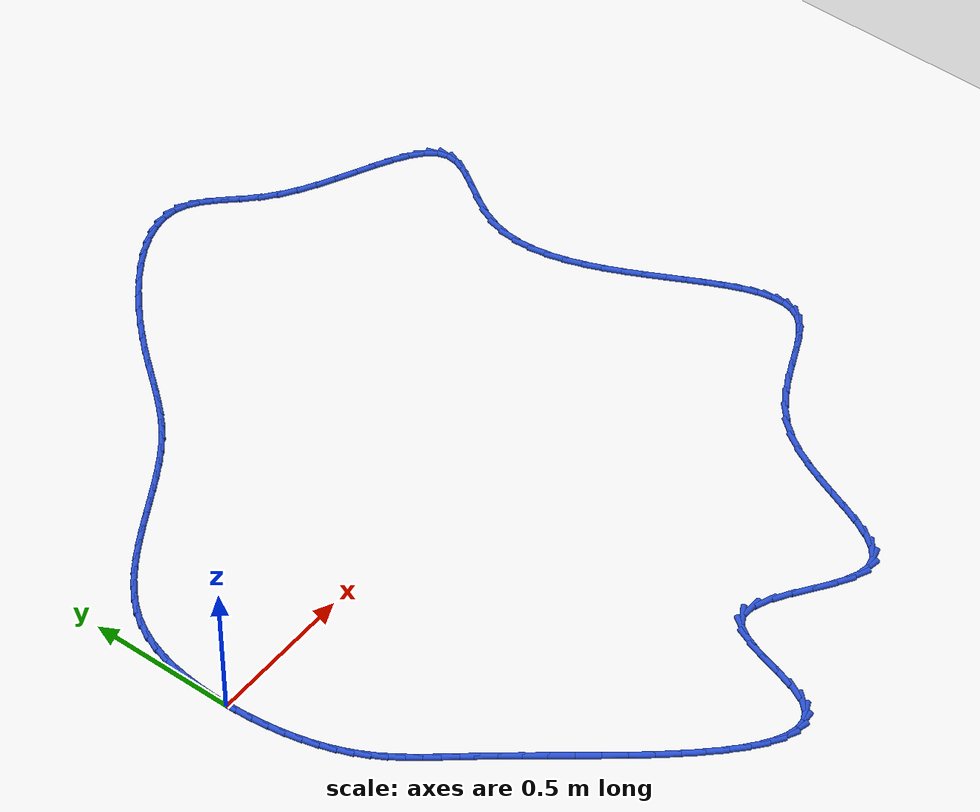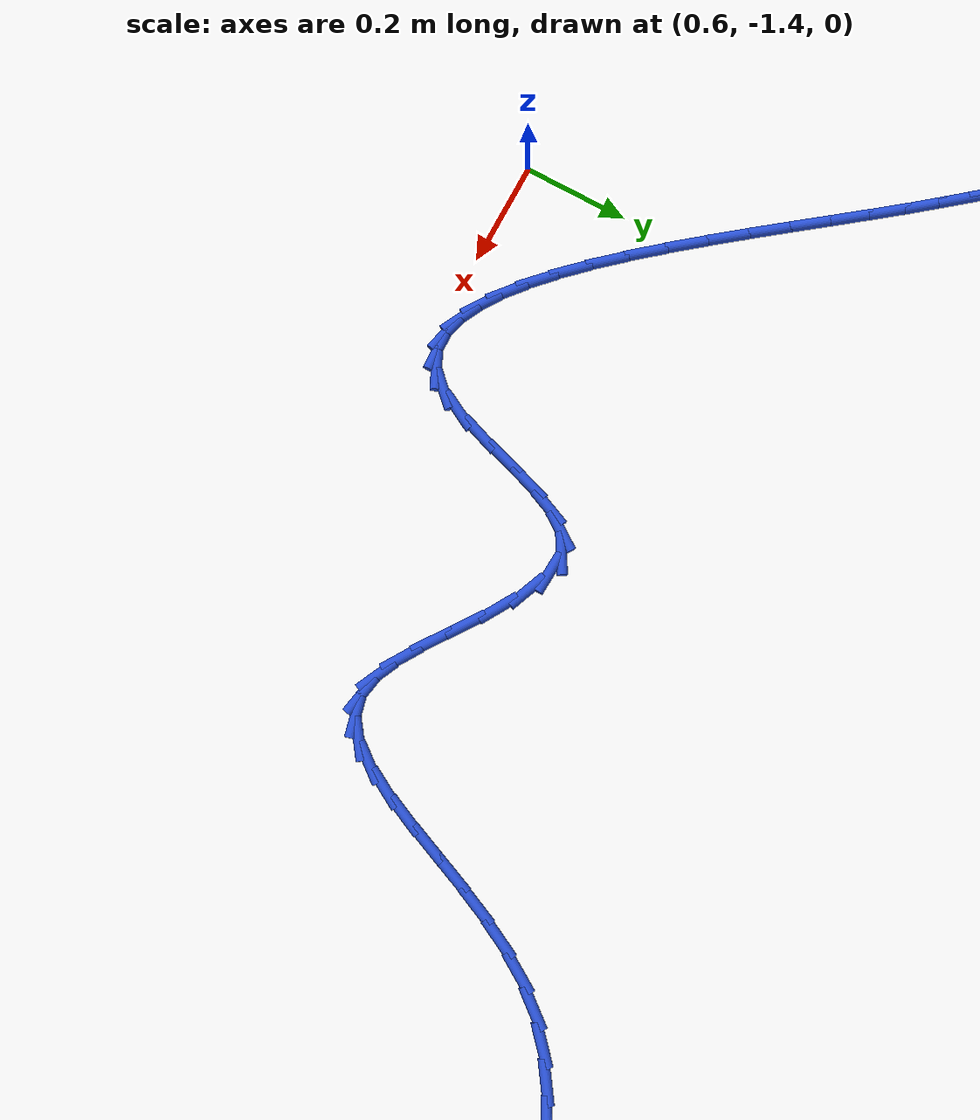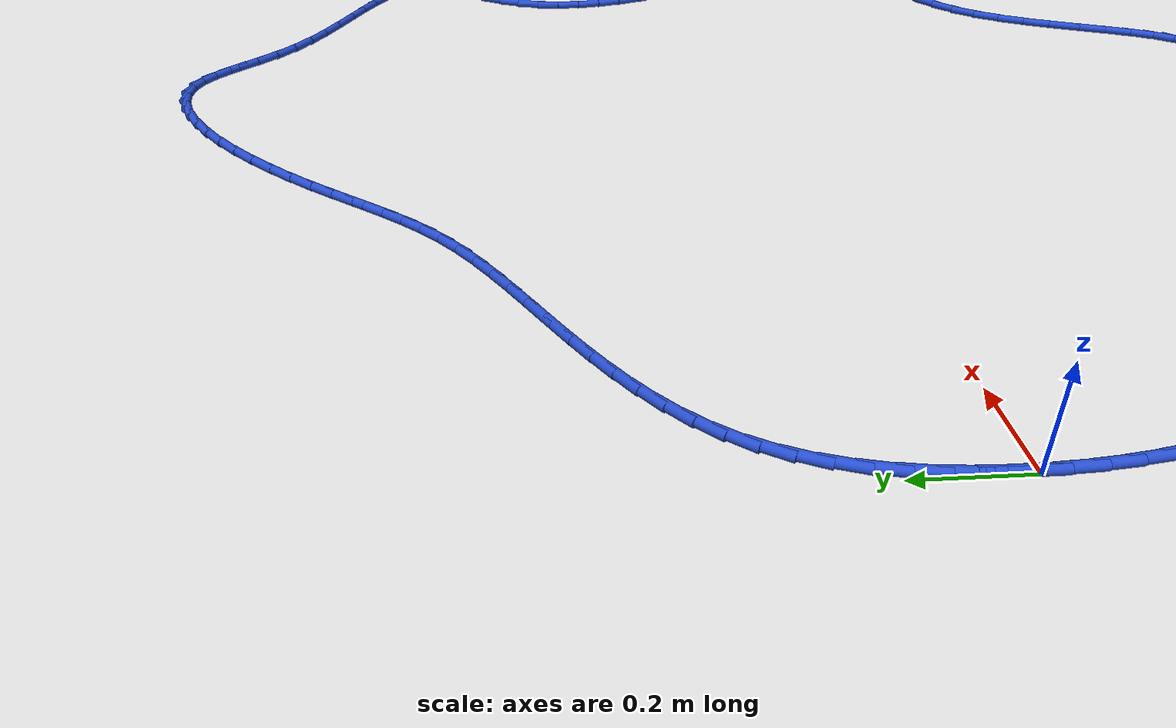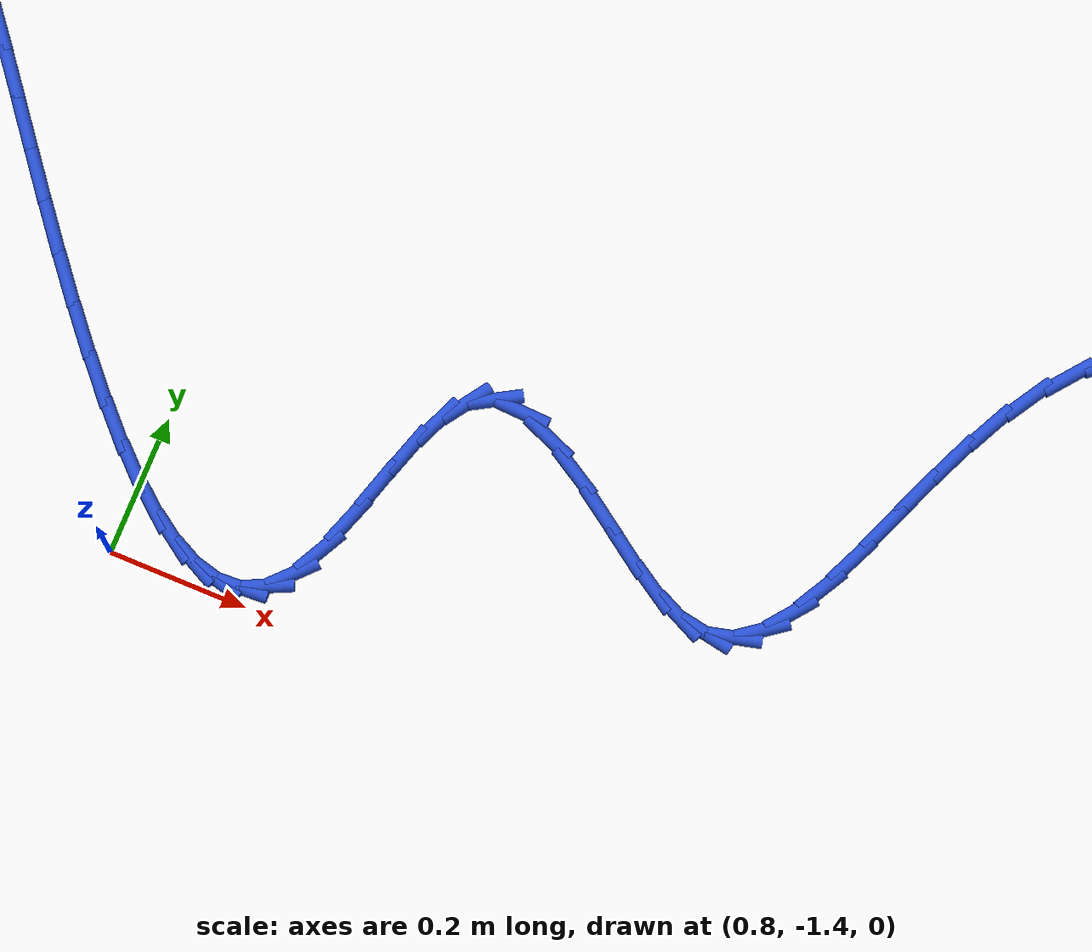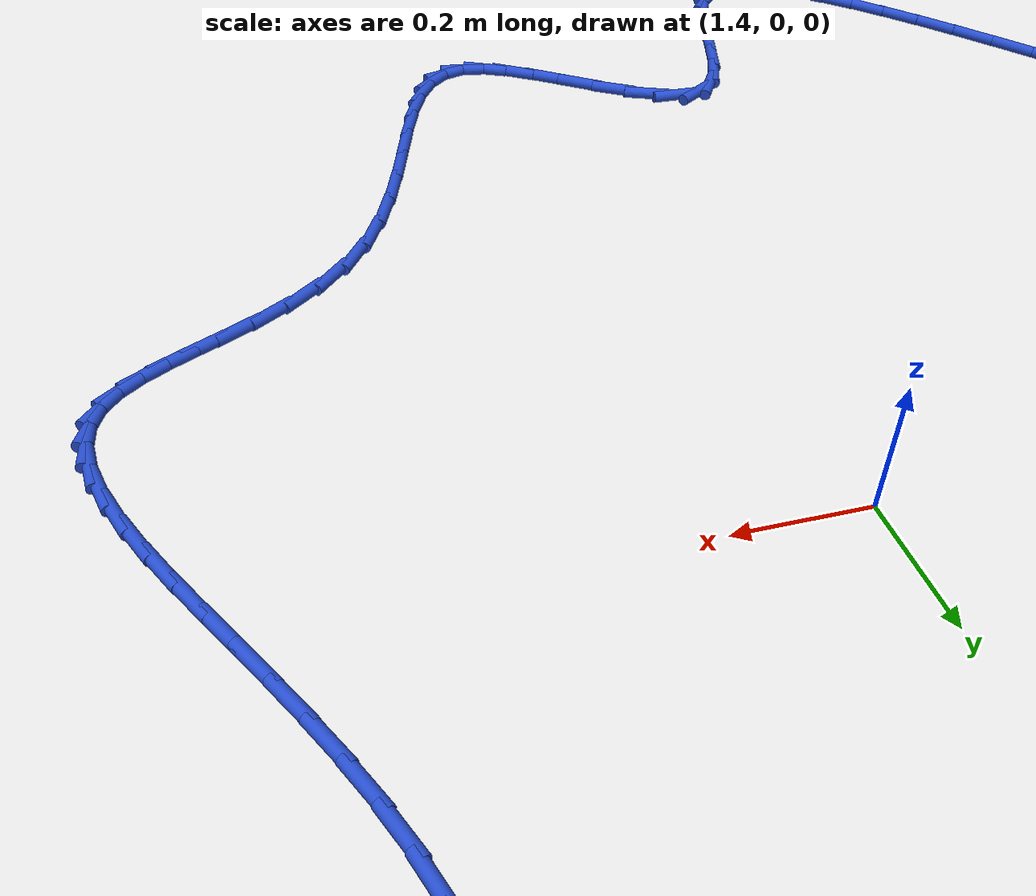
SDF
<sdf version="1.6">
 <world name="default">
  <light name="sun" type="directional">
   <pose>0 0 10 0 -0 0</pose>
   <diffuse>0.8 0.8 0.8 1</diffuse>
   <specular>0.2 0.2 0.2 1</specular>
   <attenuation>
    <range>1000</range>
    <constant>0.9</constant>
    <linear>0.01</linear>
    <quadratic>0.001</quadratic>
   </attenuation>
   <direction>-0.5 0.1 -0.9</direction>
  </light>
  <model name="ground_plane">
   <static>1</static>
   <link name="link">
    <collision name="collision">
     <geometry><plane><normal>0 0 1</normal><size>100 100</size></plane></geometry>
     <surface><friction><ode><mu>100</mu><mu2>50</mu2></ode></friction></surface>
    </collision>
    <visual name="visual">
     <cast_shadows>0</cast_shadows>
     <geometry><plane><normal>0 0 1</normal><size>100 100</size></plane></geometry>
     <material>
      <script><uri>file://media/materials/scripts/gazebo.material</uri><name>Gazebo/WhiteGlow</name></script>
     </material>
    </visual>
   </link>
  </model>
  <gravity>0 0 -9.8</gravity>
  <magnetic_field>6e-06 2.3e-05 -4.2e-05</magnetic_field>
  <atmosphere type="adiabatic"/>
  <physics name="default_physics" default="0" type="ode">
   <max_step_size>0.001</max_step_size>
   <real_time_factor>1</real_time_factor>
   <real_time_update_rate>1000</real_time_update_rate>
  </physics>
  <scene><ambient>0.4 0.4 0.4 1</ambient><background>0.7 0.7 0.7 1</background><shadows>1</shadows></scene>
  <spherical_coordinates>
   <surface_model>EARTH_WGS84</surface_model>
   <latitude_deg>0</latitude_deg>
   <longitude_deg>0</longitude_deg>
   <elevation>0</elevation>
   <heading_deg>0</heading_deg>
  </spherical_coordinates>
  <model name="line">
   <link name="link_0">
    <pose>-1.734723475976807e-18 5.551115123125783e-17 0.01 0 1.57 -1.5661314822219803</pose>
    <collision name="collision">
     <geometry><cylinder><radius>0.01</radius><length>0.08</length></cylinder></geometry>
    </collision>
    <visual name="visual">
     <material>
      <script><name>Gazebo/Blue</name><uri>file://media/materials/scripts/gazebo.material</uri></script>
     </material>
     <geometry><cylinder><radius>0.01</radius><length>0.08</length></cylinder></geometry>
    </visual>
   </link>
   <link name="link_1">
    <pose>-0.0002671970481219554 0.05727845929362262 0.01 0 1.57 1.526995578784829</pose>
    <collision name="collision">
     <geometry><cylinder><radius>0.01</radius><length>0.08</length></cylinder></geometry>
    </collision>
    <visual name="visual">
     <material>
      <script><name>Gazebo/Blue</name><uri>file://media/materials/scripts/gazebo.material</uri></script>
     </material>
     <geometry><cylinder><radius>0.01</radius><length>0.08</length></cylinder></geometry>
    </visual>
   </link>
   <link name="link_2">
    <pose>0.002229847736398396 0.1142511784565556 0.01 0 1.57 1.4708896036431018</pose>
    <collision name="collision">
     <geometry><cylinder><radius>0.01</radius><length>0.08</length></cylinder></geometry>
    </collision>
    <visual name="visual">
     <material>
      <script><name>Gazebo/Blue</name><uri>file://media/materials/scripts/gazebo.material</uri></script>
     </material>
     <geometry><cylinder><radius>0.01</radius><length>0.08</length></cylinder></geometry>
    </visual>
   </link>
   <link name="link_3">
    <pose>0.007858735817602821 0.17040503333965376 0.01 0 1.57 1.4058010821259437</pose>
    <collision name="collision">
     <geometry><cylinder><radius>0.01</radius><length>0.08</length></cylinder></geometry>
    </collision>
    <visual name="visual">
     <material>
      <script><name>Gazebo/Blue</name><uri>file://media/materials/scripts/gazebo.material</uri></script>
     </material>
     <geometry><cylinder><radius>0.01</radius><length>0.08</length></cylinder></geometry>
    </visual>
   </link>
   <link name="link_4">
    <pose>0.016987068659533096 0.22522689979377192 0.01 0 1.57 1.3302428327054945</pose>
    <collision name="collision">
     <geometry><cylinder><radius>0.01</radius><length>0.08</length></cylinder></geometry>
    </collision>
    <visual name="visual">
     <material>
      <script><name>Gazebo/Blue</name><uri>file://media/materials/scripts/gazebo.material</uri></script>
     </material>
     <geometry><cylinder><radius>0.01</radius><length>0.08</length></cylinder></geometry>
    </visual>
   </link>
   <link name="link_5">
    <pose>0.02998244772623098 0.2782036536697649 0.01 0 1.57 1.2427084562064419</pose>
    <collision name="collision">
     <geometry><cylinder><radius>0.01</radius><length>0.08</length></cylinder></geometry>
    </collision>
    <visual name="visual">
     <material>
      <script><name>Gazebo/Blue</name><uri>file://media/materials/scripts/gazebo.material</uri></script>
     </material>
     <geometry><cylinder><radius>0.01</radius><length>0.08</length></cylinder></geometry>
    </visual>
   </link>
   <link name="link_6">
    <pose>0.047212474481738306 0.32882217081848764 0.01 0 1.57 1.1419316082793176</pose>
    <collision name="collision">
     <geometry><cylinder><radius>0.01</radius><length>0.08</length></cylinder></geometry>
    </collision>
    <visual name="visual">
     <material>
      <script><name>Gazebo/Blue</name><uri>file://media/materials/scripts/gazebo.material</uri></script>
     </material>
     <geometry><cylinder><radius>0.01</radius><length>0.08</length></cylinder></geometry>
    </visual>
   </link>
   <link name="link_7">
    <pose>0.06904475039009678 0.37656932709079466 0.01 0 1.57 1.0274769942199709</pose>
    <collision name="collision">
     <geometry><cylinder><radius>0.01</radius><length>0.08</length></cylinder></geometry>
    </collision>
    <visual name="visual">
     <material>
      <script><name>Gazebo/Blue</name><uri>file://media/materials/scripts/gazebo.material</uri></script>
     </material>
     <geometry><cylinder><radius>0.01</radius><length>0.08</length></cylinder></geometry>
    </visual>
   </link>
   <link name="link_8">
    <pose>0.0958410073056266 0.4209376154864044 0.01 0 1.57 0.9097125452312507</pose>
    <collision name="collision">
     <geometry><cylinder><radius>0.01</radius><length>0.08</length></cylinder></geometry>
    </collision>
    <visual name="visual">
     <material>
      <script><name>Gazebo/Blue</name><uri>file://media/materials/scripts/gazebo.material</uri></script>
     </material>
     <geometry><cylinder><radius>0.01</radius><length>0.08</length></cylinder></geometry>
    </visual>
   </link>
   <link name="link_9">
    <pose>0.12759987050115218 0.4617670178191727 0.01 0 1.57 0.8060424598398853</pose>
    <collision name="collision">
     <geometry><cylinder><radius>0.01</radius><length>0.08</length></cylinder></geometry>
    </collision>
    <visual name="visual">
     <material>
      <script><name>Gazebo/Blue</name><uri>file://media/materials/scripts/gazebo.material</uri></script>
     </material>
     <geometry><cylinder><radius>0.01</radius><length>0.08</length></cylinder></geometry>
    </visual>
   </link>
   <link name="link_10">
    <pose>0.16375077368198546 0.4994422256738341 0.01 0 1.57 0.7191271859253768</pose>
    <collision name="collision">
     <geometry><cylinder><radius>0.01</radius><length>0.08</length></cylinder></geometry>
    </collision>
    <visual name="visual">
     <material>
      <script><name>Gazebo/Blue</name><uri>file://media/materials/scripts/gazebo.material</uri></script>
     </material>
     <geometry><cylinder><radius>0.01</radius><length>0.08</length></cylinder></geometry>
    </visual>
   </link>
   <link name="link_11">
    <pose>0.2036734349284112 0.5343955079153645 0.01 0 1.57 0.6487994551378756</pose>
    <collision name="collision">
     <geometry><cylinder><radius>0.01</radius><length>0.08</length></cylinder></geometry>
    </collision>
    <visual name="visual">
     <material>
      <script><name>Gazebo/Blue</name><uri>file://media/materials/scripts/gazebo.material</uri></script>
     </material>
     <geometry><cylinder><radius>0.01</radius><length>0.08</length></cylinder></geometry>
    </visual>
   </link>
   <link name="link_12">
    <pose>0.24674757232071393 0.5670591334087391 0.01 0 1.57 0.5940906143464005</pose>
    <collision name="collision">
     <geometry><cylinder><radius>0.01</radius><length>0.08</length></cylinder></geometry>
    </collision>
    <visual name="visual">
     <material>
      <script><name>Gazebo/Blue</name><uri>file://media/materials/scripts/gazebo.material</uri></script>
     </material>
     <geometry><cylinder><radius>0.01</radius><length>0.08</length></cylinder></geometry>
    </visual>
   </link>
   <link name="link_13">
    <pose>0.29235290393917834 0.5978653710189334 0.01 0 1.57 0.5537946082802397</pose>
    <collision name="collision">
     <geometry><cylinder><radius>0.01</radius><length>0.08</length></cylinder></geometry>
    </collision>
    <visual name="visual">
     <material>
      <script><name>Gazebo/Blue</name><uri>file://media/materials/scripts/gazebo.material</uri></script>
     </material>
     <geometry><cylinder><radius>0.01</radius><length>0.08</length></cylinder></geometry>
    </visual>
   </link>
   <link name="link_14">
    <pose>0.33986914786408895 0.627246489610923 0.01 0 1.57 0.5268137422496977</pose>
    <collision name="collision">
     <geometry><cylinder><radius>0.01</radius><length>0.08</length></cylinder></geometry>
    </collision>
    <visual name="visual">
     <material>
      <script><name>Gazebo/Blue</name><uri>file://media/materials/scripts/gazebo.material</uri></script>
     </material>
     <geometry><cylinder><radius>0.01</radius><length>0.08</length></cylinder></geometry>
    </visual>
   </link>
   <link name="link_15">
    <pose>0.38867602217573044 0.6556347580496831 0.01 0 1.57 0.5123395501668344</pose>
    <collision name="collision">
     <geometry><cylinder><radius>0.01</radius><length>0.08</length></cylinder></geometry>
    </collision>
    <visual name="visual">
     <material>
      <script><name>Gazebo/Blue</name><uri>file://media/materials/scripts/gazebo.material</uri></script>
     </material>
     <geometry><cylinder><radius>0.01</radius><length>0.08</length></cylinder></geometry>
    </visual>
   </link>
   <link name="link_16">
    <pose>0.4381532449543873 0.6834624452001891 0.01 0 1.57 0.5099362327819195</pose>
    <collision name="collision">
     <geometry><cylinder><radius>0.01</radius><length>0.08</length></cylinder></geometry>
    </collision>
    <visual name="visual">
     <material>
      <script><name>Gazebo/Blue</name><uri>file://media/materials/scripts/gazebo.material</uri></script>
     </material>
     <geometry><cylinder><radius>0.01</radius><length>0.08</length></cylinder></geometry>
    </visual>
   </link>
   <link name="link_17">
    <pose>0.4876805342803443 0.7111618199274167 0.01 0 1.57 0.5195750054899217</pose>
    <collision name="collision">
     <geometry><cylinder><radius>0.01</radius><length>0.08</length></cylinder></geometry>
    </collision>
    <visual name="visual">
     <material>
      <script><name>Gazebo/Blue</name><uri>file://media/materials/scripts/gazebo.material</uri></script>
     </material>
     <geometry><cylinder><radius>0.01</radius><length>0.08</length></cylinder></geometry>
    </visual>
   </link>
   <link name="link_18">
    <pose>0.5366376082338858 0.7391651510963408 0.01 0 1.57 0.5416440820067135</pose>
    <collision name="collision">
     <geometry><cylinder><radius>0.01</radius><length>0.08</length></cylinder></geometry>
    </collision>
    <visual name="visual">
     <material>
      <script><name>Gazebo/Blue</name><uri>file://media/materials/scripts/gazebo.material</uri></script>
     </material>
     <geometry><cylinder><radius>0.01</radius><length>0.08</length></cylinder></geometry>
    </visual>
   </link>
   <link name="link_19">
    <pose>0.584404184895297 0.7679047075719379 0.01 0 1.57 0.5769376752377415</pose>
    <collision name="collision">
     <geometry><cylinder><radius>0.01</radius><length>0.08</length></cylinder></geometry>
    </collision>
    <visual name="visual">
     <material>
      <script><name>Gazebo/Blue</name><uri>file://media/materials/scripts/gazebo.material</uri></script>
     </material>
     <geometry><cylinder><radius>0.01</radius><length>0.08</length></cylinder></geometry>
    </visual>
   </link>
   <link name="link_20">
    <pose>0.6303599823448617 0.7978127582191819 0.01 0 1.57 0.6266057498468776</pose>
    <collision name="collision">
     <geometry><cylinder><radius>0.01</radius><length>0.08</length></cylinder></geometry>
    </collision>
    <visual name="visual">
     <material>
      <script><name>Gazebo/Blue</name><uri>file://media/materials/scripts/gazebo.material</uri></script>
     </material>
     <geometry><cylinder><radius>0.01</radius><length>0.08</length></cylinder></geometry>
    </visual>
   </link>
   <link name="link_21">
    <pose>0.6738847186628651 0.8293215719030496 0.01 0 1.57 0.6918991876859012</pose>
    <collision name="collision">
     <geometry><cylinder><radius>0.01</radius><length>0.08</length></cylinder></geometry>
    </collision>
    <visual name="visual">
     <material>
      <script><name>Gazebo/Blue</name><uri>file://media/materials/scripts/gazebo.material</uri></script>
     </material>
     <geometry><cylinder><radius>0.01</radius><length>0.08</length></cylinder></geometry>
    </visual>
   </link>
   <link name="link_22">
    <pose>0.714364827107283 0.862860717970392 0.01 0 1.57 0.7637602063803552</pose>
    <collision name="collision">
     <geometry><cylinder><radius>0.01</radius><length>0.08</length></cylinder></geometry>
    </collision>
    <visual name="visual">
     <material>
      <script><name>Gazebo/Blue</name><uri>file://media/materials/scripts/gazebo.material</uri></script>
     </material>
     <geometry><cylinder><radius>0.01</radius><length>0.08</length></cylinder></geometry>
    </visual>
   </link>
   <link name="link_23">
    <pose>0.7517288890169467 0.8986418208919603 0.01 0 1.57 0.8230872295489523</pose>
    <collision name="collision">
     <geometry><cylinder><radius>0.01</radius><length>0.08</length></cylinder></geometry>
    </collision>
    <visual name="visual">
     <material>
      <script><name>Gazebo/Blue</name><uri>file://media/materials/scripts/gazebo.material</uri></script>
     </material>
     <geometry><cylinder><radius>0.01</radius><length>0.08</length></cylinder></geometry>
    </visual>
   </link>
   <link name="link_24">
    <pose>0.7868374852966593 0.9365018389963474 0.01 0 1.57 0.8658998866363601</pose>
    <collision name="collision">
     <geometry><cylinder><radius>0.01</radius><length>0.08</length></cylinder></geometry>
    </collision>
    <visual name="visual">
     <material>
      <script><name>Gazebo/Blue</name><uri>file://media/materials/scripts/gazebo.material</uri></script>
     </material>
     <geometry><cylinder><radius>0.01</radius><length>0.08</length></cylinder></geometry>
    </visual>
   </link>
   <link name="link_25">
    <pose>0.8206431311935424 0.9762407727780172 0.01 0 1.57 0.8913484481223635</pose>
    <collision name="collision">
     <geometry><cylinder><radius>0.01</radius><length>0.08</length></cylinder></geometry>
    </collision>
    <visual name="visual">
     <material>
      <script><name>Gazebo/Blue</name><uri>file://media/materials/scripts/gazebo.material</uri></script>
     </material>
     <geometry><cylinder><radius>0.01</radius><length>0.08</length></cylinder></geometry>
    </visual>
   </link>
   <link name="link_26">
    <pose>0.8540983419547166 1.0176586227314344 0.01 0 1.57 0.8997638475194427</pose>
    <collision name="collision">
     <geometry><cylinder><radius>0.01</radius><length>0.08</length></cylinder></geometry>
    </collision>
    <visual name="visual">
     <material>
      <script><name>Gazebo/Blue</name><uri>file://media/materials/scripts/gazebo.material</uri></script>
     </material>
     <geometry><cylinder><radius>0.01</radius><length>0.08</length></cylinder></geometry>
    </visual>
   </link>
   <link name="link_27">
    <pose>0.8881556328273027 1.0605553893510618 0.01 0 1.57 0.8923213004050221</pose>
    <collision name="collision">
     <geometry><cylinder><radius>0.01</radius><length>0.08</length></cylinder></geometry>
    </collision>
    <visual name="visual">
     <material>
      <script><name>Gazebo/Blue</name><uri>file://media/materials/scripts/gazebo.material</uri></script>
     </material>
     <geometry><cylinder><radius>0.01</radius><length>0.08</length></cylinder></geometry>
    </visual>
   </link>
   <link name="link_28">
    <pose>0.9237675190584217 1.1047310731313638 0.01 0 1.57 0.8707760081696162</pose>
    <collision name="collision">
     <geometry><cylinder><radius>0.01</radius><length>0.08</length></cylinder></geometry>
    </collision>
    <visual name="visual">
     <material>
      <script><name>Gazebo/Blue</name><uri>file://media/materials/scripts/gazebo.material</uri></script>
     </material>
     <geometry><cylinder><radius>0.01</radius><length>0.08</length></cylinder></geometry>
    </visual>
   </link>
   <link name="link_29">
    <pose>0.9618865158951946 1.149985674566805 0.01 0 1.57 0.8381461508184193</pose>
    <collision name="collision">
     <geometry><cylinder><radius>0.01</radius><length>0.08</length></cylinder></geometry>
    </collision>
    <visual name="visual">
     <material>
      <script><name>Gazebo/Blue</name><uri>file://media/materials/scripts/gazebo.material</uri></script>
     </material>
     <geometry><cylinder><radius>0.01</radius><length>0.08</length></cylinder></geometry>
    </visual>
   </link>
   <link name="link_30">
    <pose>1.0033143003824534 1.1960318167273614 0.01 0 1.57 0.8012724457577897</pose>
    <collision name="collision">
     <geometry><cylinder><radius>0.01</radius><length>0.08</length></cylinder></geometry>
    </collision>
    <visual name="visual">
     <material>
      <script><name>Gazebo/Blue</name><uri>file://media/materials/scripts/gazebo.material</uri></script>
     </material>
     <geometry><cylinder><radius>0.01</radius><length>0.08</length></cylinder></geometry>
    </visual>
   </link>
   <link name="link_31">
    <pose>1.047843323598448 1.2419974991304394 0.01 0 1.57 0.7610488346533506</pose>
    <collision name="collision">
     <geometry><cylinder><radius>0.01</radius><length>0.08</length></cylinder></geometry>
    </collision>
    <visual name="visual">
     <material>
      <script><name>Gazebo/Blue</name><uri>file://media/materials/scripts/gazebo.material</uri></script>
     </material>
     <geometry><cylinder><radius>0.01</radius><length>0.08</length></cylinder></geometry>
    </visual>
   </link>
   <link name="link_32">
    <pose>1.0948519377539692 1.2867708424565687 0.01 0 1.57 0.7154735530034442</pose>
    <collision name="collision">
     <geometry><cylinder><radius>0.01</radius><length>0.08</length></cylinder></geometry>
    </collision>
    <visual name="visual">
     <material>
      <script><name>Gazebo/Blue</name><uri>file://media/materials/scripts/gazebo.material</uri></script>
     </material>
     <geometry><cylinder><radius>0.01</radius><length>0.08</length></cylinder></geometry>
    </visual>
   </link>
   <link name="link_33">
    <pose>1.143717234302406 1.3292392370558117 0.01 0 1.57 0.6620981023765284</pose>
    <collision name="collision">
     <geometry><cylinder><radius>0.01</radius><length>0.08</length></cylinder></geometry>
    </collision>
    <visual name="visual">
     <material>
      <script><name>Gazebo/Blue</name><uri>file://media/materials/scripts/gazebo.material</uri></script>
     </material>
     <geometry><cylinder><radius>0.01</radius><length>0.08</length></cylinder></geometry>
    </visual>
   </link>
   <link name="link_34">
    <pose>1.1938163046971484 1.368290073278232 0.01 0 1.57 0.5976877106810827</pose>
    <collision name="collision">
     <geometry><cylinder><radius>0.01</radius><length>0.08</length></cylinder></geometry>
    </collision>
    <visual name="visual">
     <material>
      <script><name>Gazebo/Blue</name><uri>file://media/materials/scripts/gazebo.material</uri></script>
     </material>
     <geometry><cylinder><radius>0.01</radius><length>0.08</length></cylinder></geometry>
    </visual>
   </link>
   <link name="link_35">
    <pose>1.2445262403915849 1.4028107414738915 0.01 0 1.57 0.517772091851084</pose>
    <collision name="collision">
     <geometry><cylinder><radius>0.01</radius><length>0.08</length></cylinder></geometry>
    </collision>
    <visual name="visual">
     <material>
      <script><name>Gazebo/Blue</name><uri>file://media/materials/scripts/gazebo.material</uri></script>
     </material>
     <geometry><cylinder><radius>0.01</radius><length>0.08</length></cylinder></geometry>
    </visual>
   </link>
   <link name="link_36">
    <pose>1.2952241328391052 1.4316886319928541 0.01 0 1.57 0.4160923968608848</pose>
    <collision name="collision">
     <geometry><cylinder><radius>0.01</radius><length>0.08</length></cylinder></geometry>
    </collision>
    <visual name="visual">
     <material>
      <script><name>Gazebo/Blue</name><uri>file://media/materials/scripts/gazebo.material</uri></script>
     </material>
     <geometry><cylinder><radius>0.01</radius><length>0.08</length></cylinder></geometry>
    </visual>
   </link>
   <link name="link_37">
    <pose>1.345287073493098 1.4538111351851817 0.01 0 1.57 0.28416590188307844</pose>
    <collision name="collision">
     <geometry><cylinder><radius>0.01</radius><length>0.08</length></cylinder></geometry>
    </collision>
    <visual name="visual">
     <material>
      <script><name>Gazebo/Blue</name><uri>file://media/materials/scripts/gazebo.material</uri></script>
     </material>
     <geometry><cylinder><radius>0.01</radius><length>0.08</length></cylinder></geometry>
    </visual>
   </link>
   <link name="link_38">
    <pose>1.3940921538069528 1.4680656414009376 0.01 0 1.57 0.11192194011019224</pose>
    <collision name="collision">
     <geometry><cylinder><radius>0.01</radius><length>0.08</length></cylinder></geometry>
    </collision>
    <visual name="visual">
     <material>
      <script><name>Gazebo/Blue</name><uri>file://media/materials/scripts/gazebo.material</uri></script>
     </material>
     <geometry><cylinder><radius>0.01</radius><length>0.08</length></cylinder></geometry>
    </visual>
   </link>
   <link name="link_39">
    <pose>1.441016465234059 1.473339540990185 0.01 0 1.57 -0.10807005241701684</pose>
    <collision name="collision">
     <geometry><cylinder><radius>0.01</radius><length>0.08</length></cylinder></geometry>
    </collision>
    <visual name="visual">
     <material>
      <script><name>Gazebo/Blue</name><uri>file://media/materials/scripts/gazebo.material</uri></script>
     </material>
     <geometry><cylinder><radius>0.01</radius><length>0.08</length></cylinder></geometry>
    </visual>
   </link>
   <link name="link_40">
    <pose>1.4854370992278052 1.4685202243029862 0.01 0 1.57 -0.3693830136698386</pose>
    <collision name="collision">
     <geometry><cylinder><radius>0.01</radius><length>0.08</length></cylinder></geometry>
    </collision>
    <visual name="visual">
     <material>
      <script><name>Gazebo/Blue</name><uri>file://media/materials/scripts/gazebo.material</uri></script>
     </material>
     <geometry><cylinder><radius>0.01</radius><length>0.08</length></cylinder></geometry>
    </visual>
   </link>
   <link name="link_41">
    <pose>1.526749942071172 1.4525258114870325 0.01 0 1.57 -0.6061341737355761</pose>
    <collision name="collision">
     <geometry><cylinder><radius>0.01</radius><length>0.08</length></cylinder></geometry>
    </collision>
    <visual name="visual">
     <material>
      <script><name>Gazebo/Blue</name><uri>file://media/materials/scripts/gazebo.material</uri></script>
     </material>
     <geometry><cylinder><radius>0.01</radius><length>0.08</length></cylinder></geometry>
    </visual>
   </link>
   <link name="link_42">
    <pose>1.565290306556728 1.4258103975913579 0.01 0 1.57 -0.7480756750388329</pose>
    <collision name="collision">
     <geometry><cylinder><radius>0.01</radius><length>0.08</length></cylinder></geometry>
    </collision>
    <visual name="visual">
     <material>
      <script><name>Gazebo/Blue</name><uri>file://media/materials/scripts/gazebo.material</uri></script>
     </material>
     <geometry><cylinder><radius>0.01</radius><length>0.08</length></cylinder></geometry>
    </visual>
   </link>
   <link name="link_43">
    <pose>1.602750592859781 1.3910469336771893 0.01 0 1.57 -0.8082615132169183</pose>
    <collision name="collision">
     <geometry><cylinder><radius>0.01</radius><length>0.08</length></cylinder></geometry>
    </collision>
    <visual name="visual">
     <material>
      <script><name>Gazebo/Blue</name><uri>file://media/materials/scripts/gazebo.material</uri></script>
     </material>
     <geometry><cylinder><radius>0.01</radius><length>0.08</length></cylinder></geometry>
    </visual>
   </link>
   <link name="link_44">
    <pose>1.6409290872005908 1.3510814959047266 0.01 0 1.57 -0.8049863453191419</pose>
    <collision name="collision">
     <geometry><cylinder><radius>0.01</radius><length>0.08</length></cylinder></geometry>
    </collision>
    <visual name="visual">
     <material>
      <script><name>Gazebo/Blue</name><uri>file://media/materials/scripts/gazebo.material</uri></script>
     </material>
     <geometry><cylinder><radius>0.01</radius><length>0.08</length></cylinder></geometry>
    </visual>
   </link>
   <link name="link_45">
    <pose>1.6816240757994185 1.3087601604341679 0.01 0 1.57 -0.748811799929745</pose>
    <collision name="collision">
     <geometry><cylinder><radius>0.01</radius><length>0.08</length></cylinder></geometry>
    </collision>
    <visual name="visual">
     <material>
      <script><name>Gazebo/Blue</name><uri>file://media/materials/scripts/gazebo.material</uri></script>
     </material>
     <geometry><cylinder><radius>0.01</radius><length>0.08</length></cylinder></geometry>
    </visual>
   </link>
   <link name="link_46">
    <pose>1.726633844876523 1.2669290034257132 0.01 0 1.57 -0.6507750913577891</pose>
    <collision name="collision">
     <geometry><cylinder><radius>0.01</radius><length>0.08</length></cylinder></geometry>
    </collision>
    <visual name="visual">
     <material>
      <script><name>Gazebo/Blue</name><uri>file://media/materials/scripts/gazebo.material</uri></script>
     </material>
     <geometry><cylinder><radius>0.01</radius><length>0.08</length></cylinder></geometry>
    </visual>
   </link>
   <link name="link_47">
    <pose>1.777501731184049 1.2281967630934876 0.01 0 1.57 -0.561263380317154</pose>
    <collision name="collision">
     <geometry><cylinder><radius>0.01</radius><length>0.08</length></cylinder></geometry>
    </collision>
    <visual name="visual">
     <material>
      <script><name>Gazebo/Blue</name><uri>file://media/materials/scripts/gazebo.material</uri></script>
     </material>
     <geometry><cylinder><radius>0.01</radius><length>0.08</length></cylinder></geometry>
    </visual>
   </link>
   <link name="link_48">
    <pose>1.8334564337074692 1.1930174315464142 0.01 0 1.57 -0.5008988691116714</pose>
    <collision name="collision">
     <geometry><cylinder><radius>0.01</radius><length>0.08</length></cylinder></geometry>
    </collision>
    <visual name="visual">
     <material>
      <script><name>Gazebo/Blue</name><uri>file://media/materials/scripts/gazebo.material</uri></script>
     </material>
     <geometry><cylinder><radius>0.01</radius><length>0.08</length></cylinder></geometry>
    </visual>
   </link>
   <link name="link_49">
    <pose>1.8924930694966617 1.1606966329243773 0.01 0 1.57 -0.4651940257753933</pose>
    <collision name="collision">
     <geometry><cylinder><radius>0.01</radius><length>0.08</length></cylinder></geometry>
    </collision>
    <visual name="visual">
     <material>
      <script><name>Gazebo/Blue</name><uri>file://media/materials/scripts/gazebo.material</uri></script>
     </material>
     <geometry><cylinder><radius>0.01</radius><length>0.08</length></cylinder></geometry>
    </visual>
   </link>
   <link name="link_50">
    <pose>1.9525952453586797 1.1305292762345291 0.01 0 1.57 -0.45199467438119767</pose>
    <collision name="collision">
     <geometry><cylinder><radius>0.01</radius><length>0.08</length></cylinder></geometry>
    </collision>
    <visual name="visual">
     <material>
      <script><name>Gazebo/Blue</name><uri>file://media/materials/scripts/gazebo.material</uri></script>
     </material>
     <geometry><cylinder><radius>0.01</radius><length>0.08</length></cylinder></geometry>
    </visual>
   </link>
   <link name="link_51">
    <pose>2.0117465681005764 1.1018102704840236 0.01 0 1.57 -0.4619903612679493</pose>
    <collision name="collision">
     <geometry><cylinder><radius>0.01</radius><length>0.08</length></cylinder></geometry>
    </collision>
    <visual name="visual">
     <material>
      <script><name>Gazebo/Blue</name><uri>file://media/materials/scripts/gazebo.material</uri></script>
     </material>
     <geometry><cylinder><radius>0.01</radius><length>0.08</length></cylinder></geometry>
    </visual>
   </link>
   <link name="link_52">
    <pose>2.0679306445294046 1.0738345246800127 0.01 0 1.57 -0.4994982258271587</pose>
    <collision name="collision">
     <geometry><cylinder><radius>0.01</radius><length>0.08</length></cylinder></geometry>
    </collision>
    <visual name="visual">
     <material>
      <script><name>Gazebo/Blue</name><uri>file://media/materials/scripts/gazebo.material</uri></script>
     </material>
     <geometry><cylinder><radius>0.01</radius><length>0.08</length></cylinder></geometry>
    </visual>
   </link>
   <link name="link_53">
    <pose>2.1191310814522186 1.0458969478296496 0.01 0 1.57 -0.5743724013302048</pose>
    <collision name="collision">
     <geometry><cylinder><radius>0.01</radius><length>0.08</length></cylinder></geometry>
    </collision>
    <visual name="visual">
     <material>
      <script><name>Gazebo/Blue</name><uri>file://media/materials/scripts/gazebo.material</uri></script>
     </material>
     <geometry><cylinder><radius>0.01</radius><length>0.08</length></cylinder></geometry>
    </visual>
   </link>
   <link name="link_54">
    <pose>2.163331485676073 1.0172924489400874 0.01 0 1.57 -0.7056501088922148</pose>
    <collision name="collision">
     <geometry><cylinder><radius>0.01</radius><length>0.08</length></cylinder></geometry>
    </collision>
    <visual name="visual">
     <material>
      <script><name>Gazebo/Blue</name><uri>file://media/materials/scripts/gazebo.material</uri></script>
     </material>
     <geometry><cylinder><radius>0.01</radius><length>0.08</length></cylinder></geometry>
    </visual>
   </link>
   <link name="link_55">
    <pose>2.1985154640080182 0.9873159370184784 0.01 0 1.57 -0.9250836618259491</pose>
    <collision name="collision">
     <geometry><cylinder><radius>0.01</radius><length>0.08</length></cylinder></geometry>
    </collision>
    <visual name="visual">
     <material>
      <script><name>Gazebo/Blue</name><uri>file://media/materials/scripts/gazebo.material</uri></script>
     </material>
     <geometry><cylinder><radius>0.01</radius><length>0.08</length></cylinder></geometry>
    </visual>
   </link>
   <link name="link_56">
    <pose>2.222666623255111 0.9552623210719762 0.01 0 1.57 -1.2622789611679384</pose>
    <collision name="collision">
     <geometry><cylinder><radius>0.01</radius><length>0.08</length></cylinder></geometry>
    </collision>
    <visual name="visual">
     <material>
      <script><name>Gazebo/Blue</name><uri>file://media/materials/scripts/gazebo.material</uri></script>
     </material>
     <geometry><cylinder><radius>0.01</radius><length>0.08</length></cylinder></geometry>
    </visual>
   </link>
   <link name="link_57">
    <pose>2.233768570224402 0.9204265101077328 0.01 0 1.57 1.4715385782287622</pose>
    <collision name="collision">
     <geometry><cylinder><radius>0.01</radius><length>0.08</length></cylinder></geometry>
    </collision>
    <visual name="visual">
     <material>
      <script><name>Gazebo/Blue</name><uri>file://media/materials/scripts/gazebo.material</uri></script>
     </material>
     <geometry><cylinder><radius>0.01</radius><length>0.08</length></cylinder></geometry>
    </visual>
   </link>
   <link name="link_58">
    <pose>2.229954576364178 0.8821276327210775 0.01 0 1.57 1.1761902208305475</pose>
    <collision name="collision">
     <geometry><cylinder><radius>0.01</radius><length>0.08</length></cylinder></geometry>
    </collision>
    <visual name="visual">
     <material>
      <script><name>Gazebo/Blue</name><uri>file://media/materials/scripts/gazebo.material</uri></script>
     </material>
     <geometry><cylinder><radius>0.01</radius><length>0.08</length></cylinder></geometry>
    </visual>
   </link>
   <link name="link_59">
    <pose>2.2124903897407915 0.8401917327883109 0.01 0 1.57 1.034947775338001</pose>
    <collision name="collision">
     <geometry><cylinder><radius>0.01</radius><length>0.08</length></cylinder></geometry>
    </collision>
    <visual name="visual">
     <material>
      <script><name>Gazebo/Blue</name><uri>file://media/materials/scripts/gazebo.material</uri></script>
     </material>
     <geometry><cylinder><radius>0.01</radius><length>0.08</length></cylinder></geometry>
    </visual>
   </link>
   <link name="link_60">
    <pose>2.18561121317138 0.7949253883358169 0.01 0 1.57 0.986228087763419</pose>
    <collision name="collision">
     <geometry><cylinder><radius>0.01</radius><length>0.08</length></cylinder></geometry>
    </collision>
    <visual name="visual">
     <material>
      <script><name>Gazebo/Blue</name><uri>file://media/materials/scripts/gazebo.material</uri></script>
     </material>
     <geometry><cylinder><radius>0.01</radius><length>0.08</length></cylinder></geometry>
    </visual>
   </link>
   <link name="link_61">
    <pose>2.1536692805429234 0.7466541160270029 0.01 0 1.57 1.000870492364637</pose>
    <collision name="collision">
     <geometry><cylinder><radius>0.01</radius><length>0.08</length></cylinder></geometry>
    </collision>
    <visual name="visual">
     <material>
      <script><name>Gazebo/Blue</name><uri>file://media/materials/scripts/gazebo.material</uri></script>
     </material>
     <geometry><cylinder><radius>0.01</radius><length>0.08</length></cylinder></geometry>
    </visual>
   </link>
   <link name="link_62">
    <pose>2.1210168257424034 0.6957034325252764 0.01 0 1.57 1.0723823776283112</pose>
    <collision name="collision">
     <geometry><cylinder><radius>0.01</radius><length>0.08</length></cylinder></geometry>
    </collision>
    <visual name="visual">
     <material>
      <script><name>Gazebo/Blue</name><uri>file://media/materials/scripts/gazebo.material</uri></script>
     </material>
     <geometry><cylinder><radius>0.01</radius><length>0.08</length></cylinder></geometry>
    </visual>
   </link>
   <link name="link_63">
    <pose>2.092006082656802 0.6423988544940459 0.01 0 1.57 1.2066799391715672</pose>
    <collision name="collision">
     <geometry><cylinder><radius>0.01</radius><length>0.08</length></cylinder></geometry>
    </collision>
    <visual name="visual">
     <material>
      <script><name>Gazebo/Blue</name><uri>file://media/materials/scripts/gazebo.material</uri></script>
     </material>
     <geometry><cylinder><radius>0.01</radius><length>0.08</length></cylinder></geometry>
    </visual>
   </link>
   <link name="link_64">
    <pose>2.070918149971676 0.5870658910696237 0.01 0 1.57 1.3762226947626577</pose>
    <collision name="collision">
     <geometry><cylinder><radius>0.01</radius><length>0.08</length></cylinder></geometry>
    </collision>
    <visual name="visual">
     <material>
      <script><name>Gazebo/Blue</name><uri>file://media/materials/scripts/gazebo.material</uri></script>
     </material>
     <geometry><cylinder><radius>0.01</radius><length>0.08</length></cylinder></geometry>
    </visual>
   </link>
   <link name="link_65">
    <pose>2.059678227997891 0.5300298021014986 0.01 0 1.57 1.531284122406158</pose>
    <collision name="collision">
     <geometry><cylinder><radius>0.01</radius><length>0.08</length></cylinder></geometry>
    </collision>
    <visual name="visual">
     <material>
      <script><name>Gazebo/Blue</name><uri>file://media/materials/scripts/gazebo.material</uri></script>
     </material>
     <geometry><cylinder><radius>0.01</radius><length>0.08</length></cylinder></geometry>
    </visual>
   </link>
   <link name="link_66">
    <pose>2.0573689501131995 0.47161554665603 0.01 0 1.57 -1.4779967476293356</pose>
    <collision name="collision">
     <geometry><cylinder><radius>0.01</radius><length>0.08</length></cylinder></geometry>
    </collision>
    <visual name="visual">
     <material>
      <script><name>Gazebo/Blue</name><uri>file://media/materials/scripts/gazebo.material</uri></script>
     </material>
     <geometry><cylinder><radius>0.01</radius><length>0.08</length></cylinder></geometry>
    </visual>
   </link>
   <link name="link_67">
    <pose>2.0629034035655254 0.41214806585923675 0.01 0 1.57 -1.3693768004964777</pose>
    <collision name="collision">
     <geometry><cylinder><radius>0.01</radius><length>0.08</length></cylinder></geometry>
    </collision>
    <visual name="visual">
     <material>
      <script><name>Gazebo/Blue</name><uri>file://media/materials/scripts/gazebo.material</uri></script>
     </material>
     <geometry><cylinder><radius>0.01</radius><length>0.08</length></cylinder></geometry>
    </visual>
   </link>
   <link name="link_68">
    <pose>2.075194675602793 0.3519523008371395 0.01 0 1.57 -1.2826515822460836</pose>
    <collision name="collision">
     <geometry><cylinder><radius>0.01</radius><length>0.08</length></cylinder></geometry>
    </collision>
    <visual name="visual">
     <material>
      <script><name>Gazebo/Blue</name><uri>file://media/materials/scripts/gazebo.material</uri></script>
     </material>
     <geometry><cylinder><radius>0.01</radius><length>0.08</length></cylinder></geometry>
    </visual>
   </link>
   <link name="link_69">
    <pose>2.093155853472928 0.2913531927157576 0.01 0 1.57 -1.2150618189729905</pose>
    <collision name="collision">
     <geometry><cylinder><radius>0.01</radius><length>0.08</length></cylinder></geometry>
    </collision>
    <visual name="visual">
     <material>
      <script><name>Gazebo/Blue</name><uri>file://media/materials/scripts/gazebo.material</uri></script>
     </material>
     <geometry><cylinder><radius>0.01</radius><length>0.08</length></cylinder></geometry>
    </visual>
   </link>
   <link name="link_70">
    <pose>2.1157000244238553 0.23067568262111057 0.01 0 1.57 -1.1639313400429612</pose>
    <collision name="collision">
     <geometry><cylinder><radius>0.01</radius><length>0.08</length></cylinder></geometry>
    </collision>
    <visual name="visual">
     <material>
      <script><name>Gazebo/Blue</name><uri>file://media/materials/scripts/gazebo.material</uri></script>
     </material>
     <geometry><cylinder><radius>0.01</radius><length>0.08</length></cylinder></geometry>
    </visual>
   </link>
   <link name="link_71">
    <pose>2.1417402757035 0.17024471167921768 0.01 0 1.57 -1.1271277349837023</pose>
    <collision name="collision">
     <geometry><cylinder><radius>0.01</radius><length>0.08</length></cylinder></geometry>
    </collision>
    <visual name="visual">
     <material>
      <script><name>Gazebo/Blue</name><uri>file://media/materials/scripts/gazebo.material</uri></script>
     </material>
     <geometry><cylinder><radius>0.01</radius><length>0.08</length></cylinder></geometry>
    </visual>
   </link>
   <link name="link_72">
    <pose>2.170189694559787 0.11038522101609939 0.01 0 1.57 -1.1032199181109676</pose>
    <collision name="collision">
     <geometry><cylinder><radius>0.01</radius><length>0.08</length></cylinder></geometry>
    </collision>
    <visual name="visual">
     <material>
      <script><name>Gazebo/Blue</name><uri>file://media/materials/scripts/gazebo.material</uri></script>
     </material>
     <geometry><cylinder><radius>0.01</radius><length>0.08</length></cylinder></geometry>
    </visual>
   </link>
   <link name="link_73">
    <pose>2.199961368240641 0.051422151757775134 0.01 0 1.57 -1.0915316077684647</pose>
    <collision name="collision">
     <geometry><cylinder><radius>0.01</radius><length>0.08</length></cylinder></geometry>
    </collision>
    <visual name="visual">
     <material>
      <script><name>Gazebo/Blue</name><uri>file://media/materials/scripts/gazebo.material</uri></script>
     </material>
     <geometry><cylinder><radius>0.01</radius><length>0.08</length></cylinder></geometry>
    </visual>
   </link>
   <link name="link_74">
    <pose>2.2299683839939872 -0.006319554969735637 0.01 0 1.57 -1.0922042768923768</pose>
    <collision name="collision">
     <geometry><cylinder><radius>0.01</radius><length>0.08</length></cylinder></geometry>
    </collision>
    <visual name="visual">
     <material>
      <script><name>Gazebo/Blue</name><uri>file://media/materials/scripts/gazebo.material</uri></script>
     </material>
     <geometry><cylinder><radius>0.01</radius><length>0.08</length></cylinder></geometry>
    </visual>
   </link>
   <link name="link_75">
    <pose>2.259123829067751 -0.0625149580404131 0.01 0 1.57 -1.1063408221054645</pose>
    <collision name="collision">
     <geometry><cylinder><radius>0.01</radius><length>0.08</length></cylinder></geometry>
    </collision>
    <visual name="visual">
     <material>
      <script><name>Gazebo/Blue</name><uri>file://media/materials/scripts/gazebo.material</uri></script>
     </material>
     <geometry><cylinder><radius>0.01</radius><length>0.08</length></cylinder></geometry>
    </visual>
   </link>
   <link name="link_76">
    <pose>2.286340790709857 -0.11683911632823811 0.01 0 1.57 -1.1362951058141415</pose>
    <collision name="collision">
     <geometry><cylinder><radius>0.01</radius><length>0.08</length></cylinder></geometry>
    </collision>
    <visual name="visual">
     <material>
      <script><name>Gazebo/Blue</name><uri>file://media/materials/scripts/gazebo.material</uri></script>
     </material>
     <geometry><cylinder><radius>0.01</radius><length>0.08</length></cylinder></geometry>
    </visual>
   </link>
   <link name="link_77">
    <pose>2.3105323561682303 -0.16896708870719052 0.01 0 1.57 -1.1861864969444749</pose>
    <collision name="collision">
     <geometry><cylinder><radius>0.01</radius><length>0.08</length></cylinder></geometry>
    </collision>
    <visual name="visual">
     <material>
      <script><name>Gazebo/Blue</name><uri>file://media/materials/scripts/gazebo.material</uri></script>
     </material>
     <geometry><cylinder><radius>0.01</radius><length>0.08</length></cylinder></geometry>
    </visual>
   </link>
   <link name="link_78">
    <pose>2.3306116126907956 -0.21857393405124986 0.01 0 1.57 -1.2627123637039737</pose>
    <collision name="collision">
     <geometry><cylinder><radius>0.01</radius><length>0.08</length></cylinder></geometry>
    </collision>
    <visual name="visual">
     <material>
      <script><name>Gazebo/Blue</name><uri>file://media/materials/scripts/gazebo.material</uri></script>
     </material>
     <geometry><cylinder><radius>0.01</radius><length>0.08</length></cylinder></geometry>
    </visual>
   </link>
   <link name="link_79">
    <pose>2.345491647525479 -0.26533471123439817 0.01 0 1.57 -1.376138724352128</pose>
    <collision name="collision">
     <geometry><cylinder><radius>0.01</radius><length>0.08</length></cylinder></geometry>
    </collision>
    <visual name="visual">
     <material>
      <script><name>Gazebo/Blue</name><uri>file://media/materials/scripts/gazebo.material</uri></script>
     </material>
     <geometry><cylinder><radius>0.01</radius><length>0.08</length></cylinder></geometry>
    </visual>
   </link>
   <link name="link_80">
    <pose>2.3540855479202034 -0.3089244791306141 0.01 0 1.57 -1.5403558208711114</pose>
    <collision name="collision">
     <geometry><cylinder><radius>0.01</radius><length>0.08</length></cylinder></geometry>
    </collision>
    <visual name="visual">
     <material>
      <script><name>Gazebo/Blue</name><uri>file://media/materials/scripts/gazebo.material</uri></script>
     </material>
     <geometry><cylinder><radius>0.01</radius><length>0.08</length></cylinder></geometry>
    </visual>
   </link>
   <link name="link_81">
    <pose>2.355306401122896 -0.34901829661387934 0.01 0 1.57 1.3738111099971873</pose>
    <collision name="collision">
     <geometry><cylinder><radius>0.01</radius><length>0.08</length></cylinder></geometry>
    </collision>
    <visual name="visual">
     <material>
      <script><name>Gazebo/Blue</name><uri>file://media/materials/scripts/gazebo.material</uri></script>
     </material>
     <geometry><cylinder><radius>0.01</radius><length>0.08</length></cylinder></geometry>
    </visual>
   </link>
   <link name="link_82">
    <pose>2.34806729438148 -0.3852912225581739 0.01 0 1.57 1.0893216006785125</pose>
    <collision name="collision">
     <geometry><cylinder><radius>0.01</radius><length>0.08</length></cylinder></geometry>
    </collision>
    <visual name="visual">
     <material>
      <script><name>Gazebo/Blue</name><uri>file://media/materials/scripts/gazebo.material</uri></script>
     </material>
     <geometry><cylinder><radius>0.01</radius><length>0.08</length></cylinder></geometry>
    </visual>
   </link>
   <link name="link_83">
    <pose>2.3312813149438822 -0.4174183158374772 0.01 0 1.57 0.7976024774090971</pose>
    <collision name="collision">
     <geometry><cylinder><radius>0.01</radius><length>0.08</length></cylinder></geometry>
    </collision>
    <visual name="visual">
     <material>
      <script><name>Gazebo/Blue</name><uri>file://media/materials/scripts/gazebo.material</uri></script>
     </material>
     <geometry><cylinder><radius>0.01</radius><length>0.08</length></cylinder></geometry>
    </visual>
   </link>
   <link name="link_84">
    <pose>2.3041346893864136 -0.44523577363365213 0.01 0 1.57 0.5924344706142887</pose>
    <collision name="collision">
     <geometry><cylinder><radius>0.01</radius><length>0.08</length></cylinder></geometry>
    </collision>
    <visual name="visual">
     <material>
      <script><name>Gazebo/Blue</name><uri>file://media/materials/scripts/gazebo.material</uri></script>
     </material>
     <geometry><cylinder><radius>0.01</radius><length>0.08</length></cylinder></geometry>
    </visual>
   </link>
   <link name="link_85">
    <pose>2.267752929605369 -0.4697238728068877 0.01 0 1.57 0.4783433600173599</pose>
    <collision name="collision">
     <geometry><cylinder><radius>0.01</radius><length>0.08</length></cylinder></geometry>
    </collision>
    <visual name="visual">
     <material>
      <script><name>Gazebo/Blue</name><uri>file://media/materials/scripts/gazebo.material</uri></script>
     </material>
     <geometry><cylinder><radius>0.01</radius><length>0.08</length></cylinder></geometry>
    </visual>
   </link>
   <link name="link_86">
    <pose>2.2241006208641996 -0.4923579008164359 0.01 0 1.57 0.4267119151776207</pose>
    <collision name="collision">
     <geometry><cylinder><radius>0.01</radius><length>0.08</length></cylinder></geometry>
    </collision>
    <visual name="visual">
     <material>
      <script><name>Gazebo/Blue</name><uri>file://media/materials/scripts/gazebo.material</uri></script>
     </material>
     <geometry><cylinder><radius>0.01</radius><length>0.08</length></cylinder></geometry>
    </visual>
   </link>
   <link name="link_87">
    <pose>2.1751457020671645 -0.5146151235990076 0.01 0 1.57 0.4201050400710591</pose>
    <collision name="collision">
     <geometry><cylinder><radius>0.01</radius><length>0.08</length></cylinder></geometry>
    </collision>
    <visual name="visual">
     <material>
      <script><name>Gazebo/Blue</name><uri>file://media/materials/scripts/gazebo.material</uri></script>
     </material>
     <geometry><cylinder><radius>0.01</radius><length>0.08</length></cylinder></geometry>
    </visual>
   </link>
   <link name="link_88">
    <pose>2.1228561121185248 -0.5379728070913146 0.01 0 1.57 0.4502485761168221</pose>
    <collision name="collision">
     <geometry><cylinder><radius>0.01</radius><length>0.08</length></cylinder></geometry>
    </collision>
    <visual name="visual">
     <material>
      <script><name>Gazebo/Blue</name><uri>file://media/materials/scripts/gazebo.material</uri></script>
     </material>
     <geometry><cylinder><radius>0.01</radius><length>0.08</length></cylinder></geometry>
    </visual>
   </link>
   <link name="link_89">
    <pose>2.0691997899225374 -0.5639082172300687 0.01 0 1.57 0.5144902913362136</pose>
    <collision name="collision">
     <geometry><cylinder><radius>0.01</radius><length>0.08</length></cylinder></geometry>
    </collision>
    <visual name="visual">
     <material>
      <script><name>Gazebo/Blue</name><uri>file://media/materials/scripts/gazebo.material</uri></script>
     </material>
     <geometry><cylinder><radius>0.01</radius><length>0.08</length></cylinder></geometry>
    </visual>
   </link>
   <link name="link_90">
    <pose>2.016144674383462 -0.5938986199519815 0.01 0 1.57 0.6131476958005838</pose>
    <collision name="collision">
     <geometry><cylinder><radius>0.01</radius><length>0.08</length></cylinder></geometry>
    </collision>
    <visual name="visual">
     <material>
      <script><name>Gazebo/Blue</name><uri>file://media/materials/scripts/gazebo.material</uri></script>
     </material>
     <geometry><cylinder><radius>0.01</radius><length>0.08</length></cylinder></geometry>
    </visual>
   </link>
   <link name="link_91">
    <pose>1.9656587044055591 -0.629421281193764 0.01 0 1.57 0.7468023027524521</pose>
    <collision name="collision">
     <geometry><cylinder><radius>0.01</radius><length>0.08</length></cylinder></geometry>
    </collision>
    <visual name="visual">
     <material>
      <script><name>Gazebo/Blue</name><uri>file://media/materials/scripts/gazebo.material</uri></script>
     </material>
     <geometry><cylinder><radius>0.01</radius><length>0.08</length></cylinder></geometry>
    </visual>
   </link>
   <link name="link_92">
    <pose>1.9197098188930868 -0.6719534668921291 0.01 0 1.57 0.902065421191802</pose>
    <collision name="collision">
     <geometry><cylinder><radius>0.01</radius><length>0.08</length></cylinder></geometry>
    </collision>
    <visual name="visual">
     <material>
      <script><name>Gazebo/Blue</name><uri>file://media/materials/scripts/gazebo.material</uri></script>
     </material>
     <geometry><cylinder><radius>0.01</radius><length>0.08</length></cylinder></geometry>
    </visual>
   </link>
   <link name="link_93">
    <pose>1.879822426590228 -0.7224316591413881 0.01 0 1.57 1.0268395971347895</pose>
    <collision name="collision">
     <geometry><cylinder><radius>0.01</radius><length>0.08</length></cylinder></geometry>
    </collision>
    <visual name="visual">
     <material>
      <script><name>Gazebo/Blue</name><uri>file://media/materials/scripts/gazebo.material</uri></script>
     </material>
     <geometry><cylinder><radius>0.01</radius><length>0.08</length></cylinder></geometry>
    </visual>
   </link>
   <link name="link_94">
    <pose>1.845448296680701 -0.7792652289478047 0.01 0 1.57 1.1126363051756467</pose>
    <collision name="collision">
     <geometry><cylinder><radius>0.01</radius><length>0.08</length></cylinder></geometry>
    </collision>
    <visual name="visual">
     <material>
      <script><name>Gazebo/Blue</name><uri>file://media/materials/scripts/gazebo.material</uri></script>
     </material>
     <geometry><cylinder><radius>0.01</radius><length>0.08</length></cylinder></geometry>
    </visual>
   </link>
   <link name="link_95">
    <pose>1.8154342629567497 -0.840125966618846 0.01 0 1.57 1.1659597023779358</pose>
    <collision name="collision">
     <geometry><cylinder><radius>0.01</radius><length>0.08</length></cylinder></geometry>
    </collision>
    <visual name="visual">
     <material>
      <script><name>Gazebo/Blue</name><uri>file://media/materials/scripts/gazebo.material</uri></script>
     </material>
     <geometry><cylinder><radius>0.01</radius><length>0.08</length></cylinder></geometry>
    </visual>
   </link>
   <link name="link_96">
    <pose>1.7886270870784948 -0.902685574513312 0.01 0 1.57 1.1905477166966383</pose>
    <collision name="collision">
     <geometry><cylinder><radius>0.01</radius><length>0.08</length></cylinder></geometry>
    </collision>
    <visual name="visual">
     <material>
      <script><name>Gazebo/Blue</name><uri>file://media/materials/scripts/gazebo.material</uri></script>
     </material>
     <geometry><cylinder><radius>0.01</radius><length>0.08</length></cylinder></geometry>
    </visual>
   </link>
   <link name="link_97">
    <pose>1.7638735307060573 -0.964615754990007 0.01 0 1.57 1.1864339087499163</pose>
    <collision name="collision">
     <geometry><cylinder><radius>0.01</radius><length>0.08</length></cylinder></geometry>
    </collision>
    <visual name="visual">
     <material>
      <script><name>Gazebo/Blue</name><uri>file://media/materials/scripts/gazebo.material</uri></script>
     </material>
     <geometry><cylinder><radius>0.01</radius><length>0.08</length></cylinder></geometry>
    </visual>
   </link>
   <link name="link_98">
    <pose>1.7400203554995584 -1.0235882104077298 0.01 0 1.57 1.1487615380157024</pose>
    <collision name="collision">
     <geometry><cylinder><radius>0.01</radius><length>0.08</length></cylinder></geometry>
    </collision>
    <visual name="visual">
     <material>
      <script><name>Gazebo/Blue</name><uri>file://media/materials/scripts/gazebo.material</uri></script>
     </material>
     <geometry><cylinder><radius>0.01</radius><length>0.08</length></cylinder></geometry>
    </visual>
   </link>
   <link name="link_99">
    <pose>1.7159143231191183 -1.0772746431252849 0.01 0 1.57 1.0650836523124063</pose>
    <collision name="collision">
     <geometry><cylinder><radius>0.01</radius><length>0.08</length></cylinder></geometry>
    </collision>
    <visual name="visual">
     <material>
      <script><name>Gazebo/Blue</name><uri>file://media/materials/scripts/gazebo.material</uri></script>
     </material>
     <geometry><cylinder><radius>0.01</radius><length>0.08</length></cylinder></geometry>
    </visual>
   </link>
   <link name="link_100">
    <pose>1.6904021952248585 -1.1233467555014724 0.01 0 1.57 0.9102578969189291</pose>
    <collision name="collision">
     <geometry><cylinder><radius>0.01</radius><length>0.08</length></cylinder></geometry>
    </collision>
    <visual name="visual">
     <material>
      <script><name>Gazebo/Blue</name><uri>file://media/materials/scripts/gazebo.material</uri></script>
     </material>
     <geometry><cylinder><radius>0.01</radius><length>0.08</length></cylinder></geometry>
    </visual>
   </link>
   <link name="link_101">
    <pose>1.6623307334769009 -1.1594762498950932 0.01 0 1.57 0.6439148397358285</pose>
    <collision name="collision">
     <geometry><cylinder><radius>0.01</radius><length>0.08</length></cylinder></geometry>
    </collision>
    <visual name="visual">
     <material>
      <script><name>Gazebo/Blue</name><uri>file://media/materials/scripts/gazebo.material</uri></script>
     </material>
     <geometry><cylinder><radius>0.01</radius><length>0.08</length></cylinder></geometry>
    </visual>
   </link>
   <link name="link_102">
    <pose>1.6305466995353646 -1.1833348286649503 0.01 0 1.57 0.24746563778720343</pose>
    <collision name="collision">
     <geometry><cylinder><radius>0.01</radius><length>0.08</length></cylinder></geometry>
    </collision>
    <visual name="visual">
     <material>
      <script><name>Gazebo/Blue</name><uri>file://media/materials/scripts/gazebo.material</uri></script>
     </material>
     <geometry><cylinder><radius>0.01</radius><length>0.08</length></cylinder></geometry>
    </visual>
   </link>
   <link name="link_103">
    <pose>1.5938968550603718 -1.1925941941698446 0.01 0 1.57 -0.17450461990742774</pose>
    <collision name="collision">
     <geometry><cylinder><radius>0.01</radius><length>0.08</length></cylinder></geometry>
    </collision>
    <visual name="visual">
     <material>
      <script><name>Gazebo/Blue</name><uri>file://media/materials/scripts/gazebo.material</uri></script>
     </material>
     <geometry><cylinder><radius>0.01</radius><length>0.08</length></cylinder></geometry>
    </visual>
   </link>
   <link name="link_104">
    <pose>1.5512905062631321 -1.185082788801884 0.01 0 1.57 -0.44148129106460243</pose>
    <collision name="collision">
     <geometry><cylinder><radius>0.01</radius><length>0.08</length></cylinder></geometry>
    </collision>
    <visual name="visual">
     <material>
      <script><name>Gazebo/Blue</name><uri>file://media/materials/scripts/gazebo.material</uri></script>
     </material>
     <geometry><cylinder><radius>0.01</radius><length>0.08</length></cylinder></geometry>
    </visual>
   </link>
   <link name="link_105">
    <pose>1.5031063224754593 -1.1623113585345004 0.01 0 1.57 -0.5635658494570346</pose>
    <collision name="collision">
     <geometry><cylinder><radius>0.01</radius><length>0.08</length></cylinder></geometry>
    </collision>
    <visual name="visual">
     <material>
      <script><name>Gazebo/Blue</name><uri>file://media/materials/scripts/gazebo.material</uri></script>
     </material>
     <geometry><cylinder><radius>0.01</radius><length>0.08</length></cylinder></geometry>
    </visual>
   </link>
   <link name="link_106">
    <pose>1.4512096756053527 -1.1295164065374654 0.01 0 1.57 -0.6087493829037802</pose>
    <collision name="collision">
     <geometry><cylinder><radius>0.01</radius><length>0.08</length></cylinder></geometry>
    </collision>
    <visual name="visual">
     <material>
      <script><name>Gazebo/Blue</name><uri>file://media/materials/scripts/gazebo.material</uri></script>
     </material>
     <geometry><cylinder><radius>0.01</radius><length>0.08</length></cylinder></geometry>
    </visual>
   </link>
   <link name="link_107">
    <pose>1.3975319501526307 -1.0920998671118147 0.01 0 1.57 -0.6002050422156614</pose>
    <collision name="collision">
     <geometry><cylinder><radius>0.01</radius><length>0.08</length></cylinder></geometry>
    </collision>
    <visual name="visual">
     <material>
      <script><name>Gazebo/Blue</name><uri>file://media/materials/scripts/gazebo.material</uri></script>
     </material>
     <geometry><cylinder><radius>0.01</radius><length>0.08</length></cylinder></geometry>
    </visual>
   </link>
   <link name="link_108">
    <pose>1.344004530617115 -1.055463674558586 0.01 0 1.57 -0.5344881655870558</pose>
    <collision name="collision">
     <geometry><cylinder><radius>0.01</radius><length>0.08</length></cylinder></geometry>
    </collision>
    <visual name="visual">
     <material>
      <script><name>Gazebo/Blue</name><uri>file://media/materials/scripts/gazebo.material</uri></script>
     </material>
     <geometry><cylinder><radius>0.01</radius><length>0.08</length></cylinder></geometry>
    </visual>
   </link>
   <link name="link_109">
    <pose>1.2925588014986265 -1.025009763178817 0.01 0 1.57 -0.3786263361455057</pose>
    <collision name="collision">
     <geometry><cylinder><radius>0.01</radius><length>0.08</length></cylinder></geometry>
    </collision>
    <visual name="visual">
     <material>
      <script><name>Gazebo/Blue</name><uri>file://media/materials/scripts/gazebo.material</uri></script>
     </material>
     <geometry><cylinder><radius>0.01</radius><length>0.08</length></cylinder></geometry>
    </visual>
   </link>
   <link name="link_110">
    <pose>1.245126147296984 -1.0061400672735437 0.01 0 1.57 -0.04536841541199422</pose>
    <collision name="collision">
     <geometry><cylinder><radius>0.01</radius><length>0.08</length></cylinder></geometry>
    </collision>
    <visual name="visual">
     <material>
      <script><name>Gazebo/Blue</name><uri>file://media/materials/scripts/gazebo.material</uri></script>
     </material>
     <geometry><cylinder><radius>0.01</radius><length>0.08</length></cylinder></geometry>
    </visual>
   </link>
   <link name="link_111">
    <pose>1.203637952512009 -1.004256521143804 0.01 0 1.57 0.5296415931006878</pose>
    <collision name="collision">
     <geometry><cylinder><radius>0.01</radius><length>0.08</length></cylinder></geometry>
    </collision>
    <visual name="visual">
     <material>
      <script><name>Gazebo/Blue</name><uri>file://media/materials/scripts/gazebo.material</uri></script>
     </material>
     <geometry><cylinder><radius>0.01</radius><length>0.08</length></cylinder></geometry>
    </visual>
   </link>
   <link name="link_112">
    <pose>1.169790103126992 -1.0240722593952762 0.01 0 1.57 0.9711557230959347</pose>
    <collision name="collision">
     <geometry><cylinder><radius>0.01</radius><length>0.08</length></cylinder></geometry>
    </collision>
    <visual name="visual">
     <material>
      <script><name>Gazebo/Blue</name><uri>file://media/materials/scripts/gazebo.material</uri></script>
     </material>
     <geometry><cylinder><radius>0.01</radius><length>0.08</length></cylinder></geometry>
    </visual>
   </link>
   <link name="link_113">
    <pose>1.1429145992257956 -1.0633863862975745 0.01 0 1.57 1.1758360274266306</pose>
    <collision name="collision">
     <geometry><cylinder><radius>0.01</radius><length>0.08</length></cylinder></geometry>
    </collision>
    <visual name="visual">
     <material>
      <script><name>Gazebo/Blue</name><uri>file://media/materials/scripts/gazebo.material</uri></script>
     </material>
     <geometry><cylinder><radius>0.01</radius><length>0.08</length></cylinder></geometry>
    </visual>
   </link>
   <link name="link_114">
    <pose>1.1209789131187369 -1.116006956288762 0.01 0 1.57 1.2619275055778354</pose>
    <collision name="collision">
     <geometry><cylinder><radius>0.01</radius><length>0.08</length></cylinder></geometry>
    </collision>
    <visual name="visual">
     <material>
      <script><name>Gazebo/Blue</name><uri>file://media/materials/scripts/gazebo.material</uri></script>
     </material>
     <geometry><cylinder><radius>0.01</radius><length>0.08</length></cylinder></geometry>
    </visual>
   </link>
   <link name="link_115">
    <pose>1.1019340105336337 -1.1756937443987663 0.01 0 1.57 1.2785919779409618</pose>
    <collision name="collision">
     <geometry><cylinder><radius>0.01</radius><length>0.08</length></cylinder></geometry>
    </collision>
    <visual name="visual">
     <material>
      <script><name>Gazebo/Blue</name><uri>file://media/materials/scripts/gazebo.material</uri></script>
     </material>
     <geometry><cylinder><radius>0.01</radius><length>0.08</length></cylinder></geometry>
    </visual>
   </link>
   <link name="link_116">
    <pose>1.0837308571983046 -1.236206525657512 0.01 0 1.57 1.2320865841872812</pose>
    <collision name="collision">
     <geometry><cylinder><radius>0.01</radius><length>0.08</length></cylinder></geometry>
    </collision>
    <visual name="visual">
     <material>
      <script><name>Gazebo/Blue</name><uri>file://media/materials/scripts/gazebo.material</uri></script>
     </material>
     <geometry><cylinder><radius>0.01</radius><length>0.08</length></cylinder></geometry>
    </visual>
   </link>
   <link name="link_117">
    <pose>1.0643204188405693 -1.2913050750949246 0.01 0 1.57 1.0908135275455617</pose>
    <collision name="collision">
     <geometry><cylinder><radius>0.01</radius><length>0.08</length></cylinder></geometry>
    </collision>
    <visual name="visual">
     <material>
      <script><name>Gazebo/Blue</name><uri>file://media/materials/scripts/gazebo.material</uri></script>
     </material>
     <geometry><cylinder><radius>0.01</radius><length>0.08</length></cylinder></geometry>
    </visual>
   </link>
   <link name="link_118">
    <pose>1.0416731814579454 -1.3348081805816396 0.01 0 1.57 0.8153977529518763</pose>
    <collision name="collision">
     <geometry><cylinder><radius>0.01</radius><length>0.08</length></cylinder></geometry>
    </collision>
    <visual name="visual">
     <material>
      <script><name>Gazebo/Blue</name><uri>file://media/materials/scripts/gazebo.material</uri></script>
     </material>
     <geometry><cylinder><radius>0.01</radius><length>0.08</length></cylinder></geometry>
    </visual>
   </link>
   <link name="link_119">
    <pose>1.014717817710756 -1.3634313787406962 0.01 0 1.57 0.4409889785306531</pose>
    <collision name="collision">
     <geometry><cylinder><radius>0.01</radius><length>0.08</length></cylinder></geometry>
    </collision>
    <visual name="visual">
     <material>
      <script><name>Gazebo/Blue</name><uri>file://media/materials/scripts/gazebo.material</uri></script>
     </material>
     <geometry><cylinder><radius>0.01</radius><length>0.08</length></cylinder></geometry>
    </visual>
   </link>
   <link name="link_120">
    <pose>0.9837571513578881 -1.3780444807586554 0.01 0 1.57 0.051856923489776774</pose>
    <collision name="collision">
     <geometry><cylinder><radius>0.01</radius><length>0.08</length></cylinder></geometry>
    </collision>
    <visual name="visual">
     <material>
      <script><name>Gazebo/Blue</name><uri>file://media/materials/scripts/gazebo.material</uri></script>
     </material>
     <geometry><cylinder><radius>0.01</radius><length>0.08</length></cylinder></geometry>
    </visual>
   </link>
   <link name="link_121">
    <pose>0.9492001243974414 -1.3798381099237047 0.01 0 1.57 -0.25490561904372655</pose>
    <collision name="collision">
     <geometry><cylinder><radius>0.01</radius><length>0.08</length></cylinder></geometry>
    </collision>
    <visual name="visual">
     <material>
      <script><name>Gazebo/Blue</name><uri>file://media/materials/scripts/gazebo.material</uri></script>
     </material>
     <geometry><cylinder><radius>0.01</radius><length>0.08</length></cylinder></geometry>
    </visual>
   </link>
   <link name="link_122">
    <pose>0.9114556788275154 -1.37000288952403 0.01 0 1.57 -0.46388419939168096</pose>
    <collision name="collision">
     <geometry><cylinder><radius>0.01</radius><length>0.08</length></cylinder></geometry>
    </collision>
    <visual name="visual">
     <material>
      <script><name>Gazebo/Blue</name><uri>file://media/materials/scripts/gazebo.material</uri></script>
     </material>
     <geometry><cylinder><radius>0.01</radius><length>0.08</length></cylinder></geometry>
    </visual>
   </link>
   <link name="link_123">
    <pose>0.8709327566462087 -1.349729442847818 0.01 0 1.57 -0.602801455201303</pose>
    <collision name="collision">
     <geometry><cylinder><radius>0.01</radius><length>0.08</length></cylinder></geometry>
    </collision>
    <visual name="visual">
     <material>
      <script><name>Gazebo/Blue</name><uri>file://media/materials/scripts/gazebo.material</uri></script>
     </material>
     <geometry><cylinder><radius>0.01</radius><length>0.08</length></cylinder></geometry>
    </visual>
   </link>
   <link name="link_124">
    <pose>0.8280402998516205 -1.3202083931832556 0.01 0 1.57 -0.6973704515516351</pose>
    <collision name="collision">
     <geometry><cylinder><radius>0.01</radius><length>0.08</length></cylinder></geometry>
    </collision>
    <visual name="visual">
     <material>
      <script><name>Gazebo/Blue</name><uri>file://media/materials/scripts/gazebo.material</uri></script>
     </material>
     <geometry><cylinder><radius>0.01</radius><length>0.08</length></cylinder></geometry>
    </visual>
   </link>
   <link name="link_125">
    <pose>0.7831872504418511 -1.2826303638185297 0.01 0 1.57 -0.7638238120553639</pose>
    <collision name="collision">
     <geometry><cylinder><radius>0.01</radius><length>0.08</length></cylinder></geometry>
    </collision>
    <visual name="visual">
     <material>
      <script><name>Gazebo/Blue</name><uri>file://media/materials/scripts/gazebo.material</uri></script>
     </material>
     <geometry><cylinder><radius>0.01</radius><length>0.08</length></cylinder></geometry>
    </visual>
   </link>
   <link name="link_126">
    <pose>0.7367825504149987 -1.2381859780418267 0.01 0 1.57 -0.811733584394263</pose>
    <collision name="collision">
     <geometry><cylinder><radius>0.01</radius><length>0.08</length></cylinder></geometry>
    </collision>
    <visual name="visual">
     <material>
      <script><name>Gazebo/Blue</name><uri>file://media/materials/scripts/gazebo.material</uri></script>
     </material>
     <geometry><cylinder><radius>0.01</radius><length>0.08</length></cylinder></geometry>
    </visual>
   </link>
   <link name="link_127">
    <pose>0.6892351417691639 -1.1880658591413342 0.01 0 1.57 -0.8467872964309262</pose>
    <collision name="collision">
     <geometry><cylinder><radius>0.01</radius><length>0.08</length></cylinder></geometry>
    </collision>
    <visual name="visual">
     <material>
      <script><name>Gazebo/Blue</name><uri>file://media/materials/scripts/gazebo.material</uri></script>
     </material>
     <geometry><cylinder><radius>0.01</radius><length>0.08</length></cylinder></geometry>
    </visual>
   </link>
   <link name="link_128">
    <pose>0.6409539665024443 -1.1334606304052373 0.01 0 1.57 -0.8724379436107929</pose>
    <collision name="collision">
     <geometry><cylinder><radius>0.01</radius><length>0.08</length></cylinder></geometry>
    </collision>
    <visual name="visual">
     <material>
      <script><name>Gazebo/Blue</name><uri>file://media/materials/scripts/gazebo.material</uri></script>
     </material>
     <geometry><cylinder><radius>0.01</radius><length>0.08</length></cylinder></geometry>
    </visual>
   </link>
   <link name="link_129">
    <pose>0.5923479666129398 -1.0755609151217227 0.01 0 1.57 -0.8908033180707602</pose>
    <collision name="collision">
     <geometry><cylinder><radius>0.01</radius><length>0.08</length></cylinder></geometry>
    </collision>
    <visual name="visual">
     <material>
      <script><name>Gazebo/Blue</name><uri>file://media/materials/scripts/gazebo.material</uri></script>
     </material>
     <geometry><cylinder><radius>0.01</radius><length>0.08</length></cylinder></geometry>
    </visual>
   </link>
   <link name="link_130">
    <pose>0.5438260840987504 -1.0155573365789794 0.01 0 1.57 -0.9031484057669649</pose>
    <collision name="collision">
     <geometry><cylinder><radius>0.01</radius><length>0.08</length></cylinder></geometry>
    </collision>
    <visual name="visual">
     <material>
      <script><name>Gazebo/Blue</name><uri>file://media/materials/scripts/gazebo.material</uri></script>
     </material>
     <geometry><cylinder><radius>0.01</radius><length>0.08</length></cylinder></geometry>
    </visual>
   </link>
   <link name="link_131">
    <pose>0.4957972609579745 -0.9546405180651913 0.01 0 1.57 -0.9101353348853791</pose>
    <collision name="collision">
     <geometry><cylinder><radius>0.01</radius><length>0.08</length></cylinder></geometry>
    </collision>
    <visual name="visual">
     <material>
      <script><name>Gazebo/Blue</name><uri>file://media/materials/scripts/gazebo.material</uri></script>
     </material>
     <geometry><cylinder><radius>0.01</radius><length>0.08</length></cylinder></geometry>
    </visual>
   </link>
   <link name="link_132">
    <pose>0.44867043918871213 -0.8940010828685472 0.01 0 1.57 -0.9119296395037867</pose>
    <collision name="collision">
     <geometry><cylinder><radius>0.01</radius><length>0.08</length></cylinder></geometry>
    </collision>
    <visual name="visual">
     <material>
      <script><name>Gazebo/Blue</name><uri>file://media/materials/scripts/gazebo.material</uri></script>
     </material>
     <geometry><cylinder><radius>0.01</radius><length>0.08</length></cylinder></geometry>
    </visual>
   </link>
   <link name="link_133">
    <pose>0.4028545607890613 -0.8348296542772315 0.01 0 1.57 -0.9081939196930185</pose>
    <collision name="collision">
     <geometry><cylinder><radius>0.01</radius><length>0.08</length></cylinder></geometry>
    </collision>
    <visual name="visual">
     <material>
      <script><name>Gazebo/Blue</name><uri>file://media/materials/scripts/gazebo.material</uri></script>
     </material>
     <geometry><cylinder><radius>0.01</radius><length>0.08</length></cylinder></geometry>
    </visual>
   </link>
   <link name="link_134">
    <pose>0.3587585677571222 -0.778316855579433 0.01 0 1.57 -0.8980597775120849</pose>
    <collision name="collision">
     <geometry><cylinder><radius>0.01</radius><length>0.08</length></cylinder></geometry>
    </collision>
    <visual name="visual">
     <material>
      <script><name>Gazebo/Blue</name><uri>file://media/materials/scripts/gazebo.material</uri></script>
     </material>
     <geometry><cylinder><radius>0.01</radius><length>0.08</length></cylinder></geometry>
    </visual>
   </link>
   <link name="link_135">
    <pose>0.31678905430629095 -0.7256388558164238 0.01 0 1.57 -0.8862975275433108</pose>
    <collision name="collision">
     <geometry><cylinder><radius>0.01</radius><length>0.08</length></cylinder></geometry>
    </collision>
    <visual name="visual">
     <material>
      <script><name>Gazebo/Blue</name><uri>file://media/materials/scripts/gazebo.material</uri></script>
     </material>
     <geometry><cylinder><radius>0.01</radius><length>0.08</length></cylinder></geometry>
    </visual>
   </link>
   <link name="link_136">
    <pose>0.27721993408971185 -0.6771549699220258 0.01 0 1.57 -0.8832141395624851</pose>
    <collision name="collision">
     <geometry><cylinder><radius>0.01</radius><length>0.08</length></cylinder></geometry>
    </collision>
    <visual name="visual">
     <material>
      <script><name>Gazebo/Blue</name><uri>file://media/materials/scripts/gazebo.material</uri></script>
     </material>
     <geometry><cylinder><radius>0.01</radius><length>0.08</length></cylinder></geometry>
    </visual>
   </link>
   <link name="link_137">
    <pose>0.2401240399161545 -0.6319865491574 0.01 0 1.57 -0.8918176510583953</pose>
    <collision name="collision">
     <geometry><cylinder><radius>0.01</radius><length>0.08</length></cylinder></geometry>
    </collision>
    <visual name="visual">
     <material>
      <script><name>Gazebo/Blue</name><uri>file://media/materials/scripts/gazebo.material</uri></script>
     </material>
     <geometry><cylinder><radius>0.01</radius><length>0.08</length></cylinder></geometry>
    </visual>
   </link>
   <link name="link_138">
    <pose>0.2055574310865524 -0.5891516778940697 0.01 0 1.57 -0.9140250797751732</pose>
    <collision name="collision">
     <geometry><cylinder><radius>0.01</radius><length>0.08</length></cylinder></geometry>
    </collision>
    <visual name="visual">
     <material>
      <script><name>Gazebo/Blue</name><uri>file://media/materials/scripts/gazebo.material</uri></script>
     </material>
     <geometry><cylinder><radius>0.01</radius><length>0.08</length></cylinder></geometry>
    </visual>
   </link>
   <link name="link_139">
    <pose>0.1735761669018369 -0.5476684405035549 0.01 0 1.57 -0.9509808492791466</pose>
    <collision name="collision">
     <geometry><cylinder><radius>0.01</radius><length>0.08</length></cylinder></geometry>
    </collision>
    <visual name="visual">
     <material>
      <script><name>Gazebo/Blue</name><uri>file://media/materials/scripts/gazebo.material</uri></script>
     </material>
     <geometry><cylinder><radius>0.01</radius><length>0.08</length></cylinder></geometry>
    </visual>
   </link>
   <link name="link_140">
    <pose>0.14423630666294177 -0.5065549213573786 0.01 0 1.57 -1.0025390201718276</pose>
    <collision name="collision">
     <geometry><cylinder><radius>0.01</radius><length>0.08</length></cylinder></geometry>
    </collision>
    <visual name="visual">
     <material>
      <script><name>Gazebo/Blue</name><uri>file://media/materials/scripts/gazebo.material</uri></script>
     </material>
     <geometry><cylinder><radius>0.01</radius><length>0.08</length></cylinder></geometry>
    </visual>
   </link>
   <link name="link_141">
    <pose>0.11759390967079866 -0.46482920482706136 0.01 0 1.57 -1.0668378199420805</pose>
    <collision name="collision">
     <geometry><cylinder><radius>0.01</radius><length>0.08</length></cylinder></geometry>
    </collision>
    <visual name="visual">
     <material>
      <script><name>Gazebo/Blue</name><uri>file://media/materials/scripts/gazebo.material</uri></script>
     </material>
     <geometry><cylinder><radius>0.01</radius><length>0.08</length></cylinder></geometry>
    </visual>
   </link>
   <link name="link_142">
    <pose>0.09370503522634085 -0.42150937528412574 0.01 0 1.57 -1.1395908849427907</pose>
    <collision name="collision">
     <geometry><cylinder><radius>0.01</radius><length>0.08</length></cylinder></geometry>
    </collision>
    <visual name="visual">
     <material>
      <script><name>Gazebo/Blue</name><uri>file://media/materials/scripts/gazebo.material</uri></script>
     </material>
     <geometry><cylinder><radius>0.01</radius><length>0.08</length></cylinder></geometry>
    </visual>
   </link>
   <link name="link_143">
    <pose>0.07262009124677343 -0.3756805922220617 0.01 0 1.57 -1.2099736559284424</pose>
    <collision name="collision">
     <geometry><cylinder><radius>0.01</radius><length>0.08</length></cylinder></geometry>
    </collision>
    <visual name="visual">
     <material>
      <script><name>Gazebo/Blue</name><uri>file://media/materials/scripts/gazebo.material</uri></script>
     </material>
     <geometry><cylinder><radius>0.01</radius><length>0.08</length></cylinder></geometry>
    </visual>
   </link>
   <link name="link_144">
    <pose>0.05432478325521576 -0.32719595466629475 0.01 0 1.57 -1.2735343553523955</pose>
    <collision name="collision">
     <geometry><cylinder><radius>0.01</radius><length>0.08</length></cylinder></geometry>
    </collision>
    <visual name="visual">
     <material>
      <script><name>Gazebo/Blue</name><uri>file://media/materials/scripts/gazebo.material</uri></script>
     </material>
     <geometry><cylinder><radius>0.01</radius><length>0.08</length></cylinder></geometry>
    </visual>
   </link>
   <link name="link_145">
    <pose>0.038763540925897455 -0.27639845628257004 0.01 0 1.57 -1.3312918094955395</pose>
    <collision name="collision">
     <geometry><cylinder><radius>0.01</radius><length>0.08</length></cylinder></geometry>
    </collision>
    <visual name="visual">
     <material>
      <script><name>Gazebo/Blue</name><uri>file://media/materials/scripts/gazebo.material</uri></script>
     </material>
     <geometry><cylinder><radius>0.01</radius><length>0.08</length></cylinder></geometry>
    </visual>
   </link>
   <link name="link_146">
    <pose>0.025880126709878253 -0.22363900987246985 0.01 0 1.57 -1.3842518438351714</pose>
    <collision name="collision">
     <geometry><cylinder><radius>0.01</radius><length>0.08</length></cylinder></geometry>
    </collision>
    <visual name="visual">
     <material>
      <script><name>Gazebo/Blue</name><uri>file://media/materials/scripts/gazebo.material</uri></script>
     </material>
     <geometry><cylinder><radius>0.01</radius><length>0.08</length></cylinder></geometry>
    </visual>
   </link>
   <link name="link_147">
    <pose>0.015618303058218663 -0.16926852823757862 0.01 0 1.57 -1.4333194456509997</pose>
    <collision name="collision">
     <geometry><cylinder><radius>0.01</radius><length>0.08</length></cylinder></geometry>
    </collision>
    <visual name="visual">
     <material>
      <script><name>Gazebo/Blue</name><uri>file://media/materials/scripts/gazebo.material</uri></script>
     </material>
     <geometry><cylinder><radius>0.01</radius><length>0.08</length></cylinder></geometry>
    </visual>
   </link>
   <link name="link_148">
    <pose>0.00792183242197903 -0.11363792417948133 0.01 0 1.57 -1.4793055162316011</pose>
    <collision name="collision">
     <geometry><cylinder><radius>0.01</radius><length>0.08</length></cylinder></geometry>
    </collision>
    <visual name="visual">
     <material>
      <script><name>Gazebo/Blue</name><uri>file://media/materials/scripts/gazebo.material</uri></script>
     </material>
     <geometry><cylinder><radius>0.01</radius><length>0.08</length></cylinder></geometry>
    </visual>
   </link>
   <link name="link_149">
    <pose>0.002734477252219339 -0.05709811049975985 0.01 0 1.57 -1.5229420359662047</pose>
    <collision name="collision">
     <geometry><cylinder><radius>0.01</radius><length>0.08</length></cylinder></geometry>
    </collision>
    <visual name="visual">
     <material>
      <script><name>Gazebo/Blue</name><uri>file://media/materials/scripts/gazebo.material</uri></script>
     </material>
     <geometry><cylinder><radius>0.01</radius><length>0.08</length></cylinder></geometry>
    </visual>
   </link>
   <link name="link_150">
    <pose>-1.734723475976807e-17 1.1102230246251565e-16 0.01 0 1.57 -1.5649010287495408</pose>
    <collision name="collision">
     <geometry><cylinder><radius>0.01</radius><length>0.08</length></cylinder></geometry>
    </collision>
    <visual name="visual">
     <material>
      <script><name>Gazebo/Blue</name><uri>file://media/materials/scripts/gazebo.material</uri></script>
     </material>
     <geometry><cylinder><radius>0.01</radius><length>0.08</length></cylinder></geometry>
    </visual>
   </link>
   <link name="link_151">
    <pose>-0.0003378368836188701 0.057305494518217544 0.01 0 1.57 -1.5649010287495404</pose>
    <collision name="collision">
     <geometry><cylinder><radius>0.01</radius><length>0.08</length></cylinder></geometry>
    </collision>
    <visual name="visual">
     <material>
      <script><name>Gazebo/Blue</name><uri>file://media/materials/scripts/gazebo.material</uri></script>
     </material>
     <geometry><cylinder><radius>0.01</radius><length>0.08</length></cylinder></geometry>
    </visual>
   </link>
  </model>
 </world>
</sdf>
